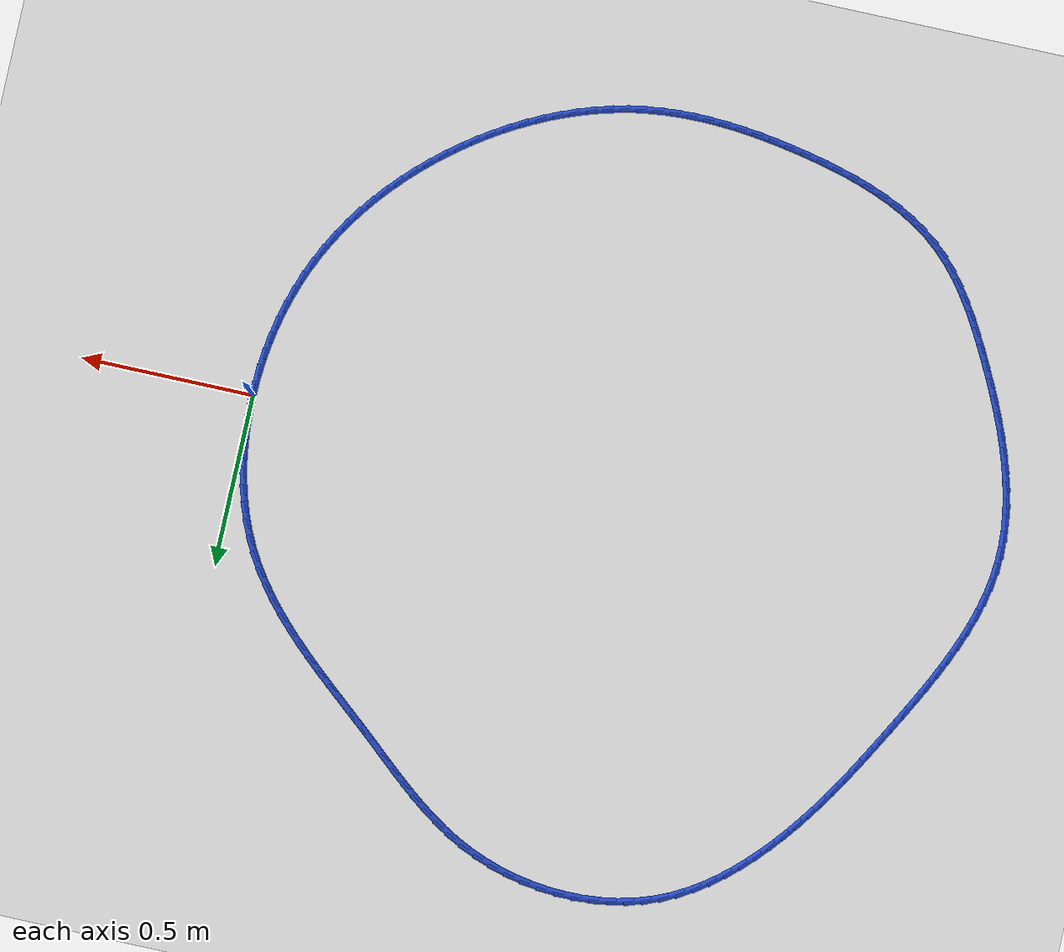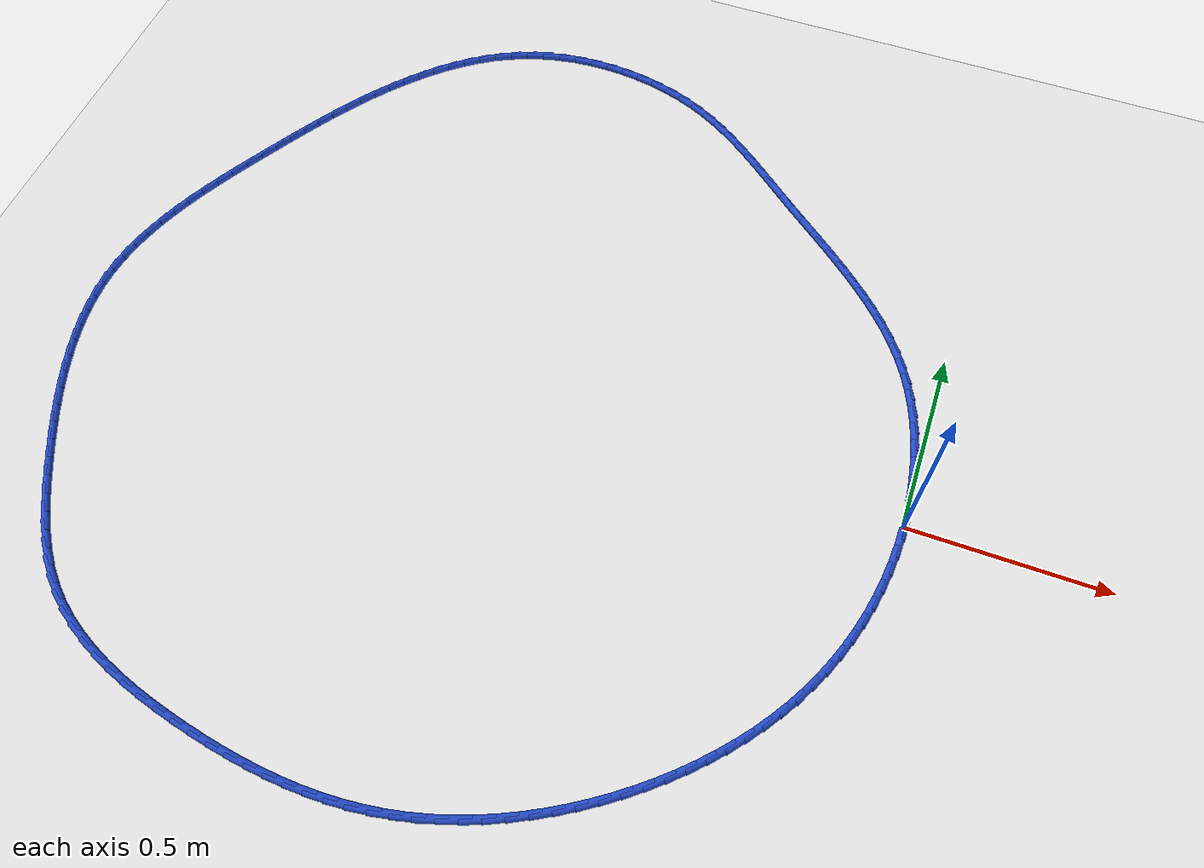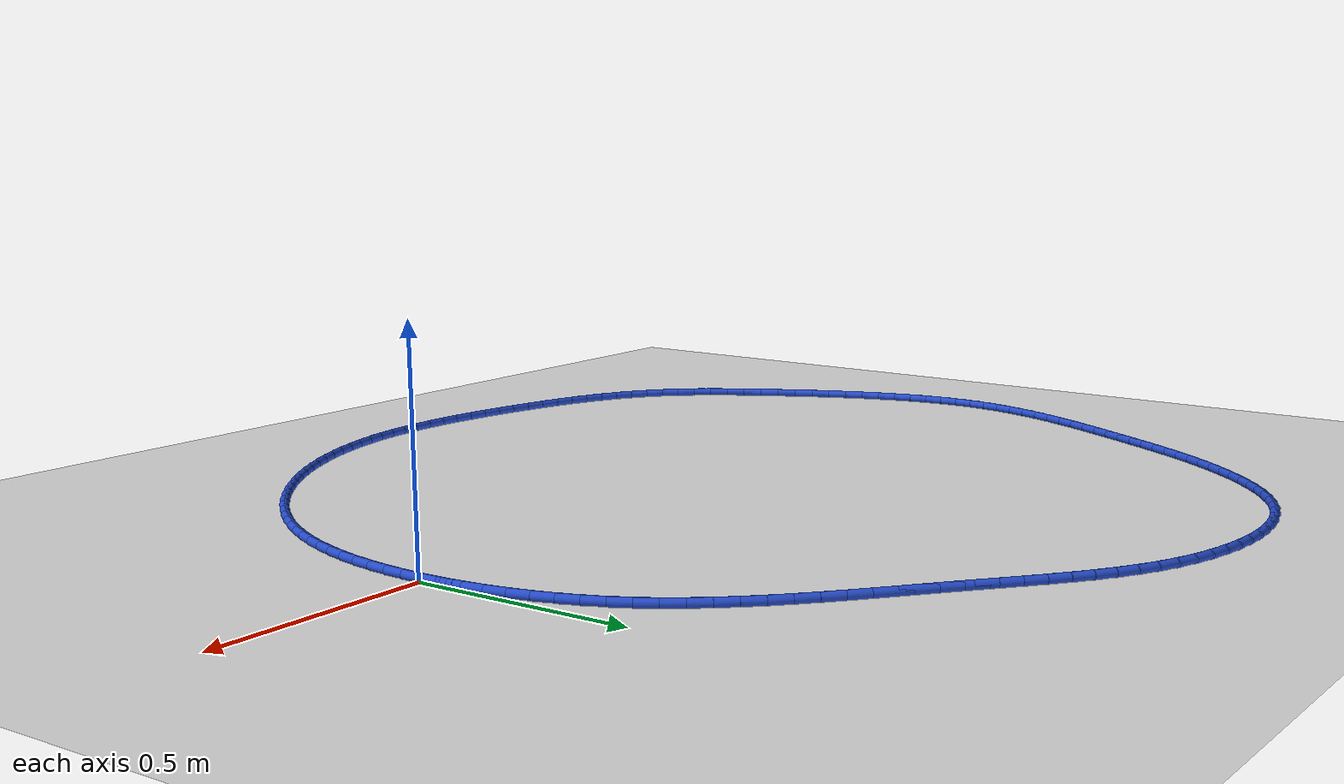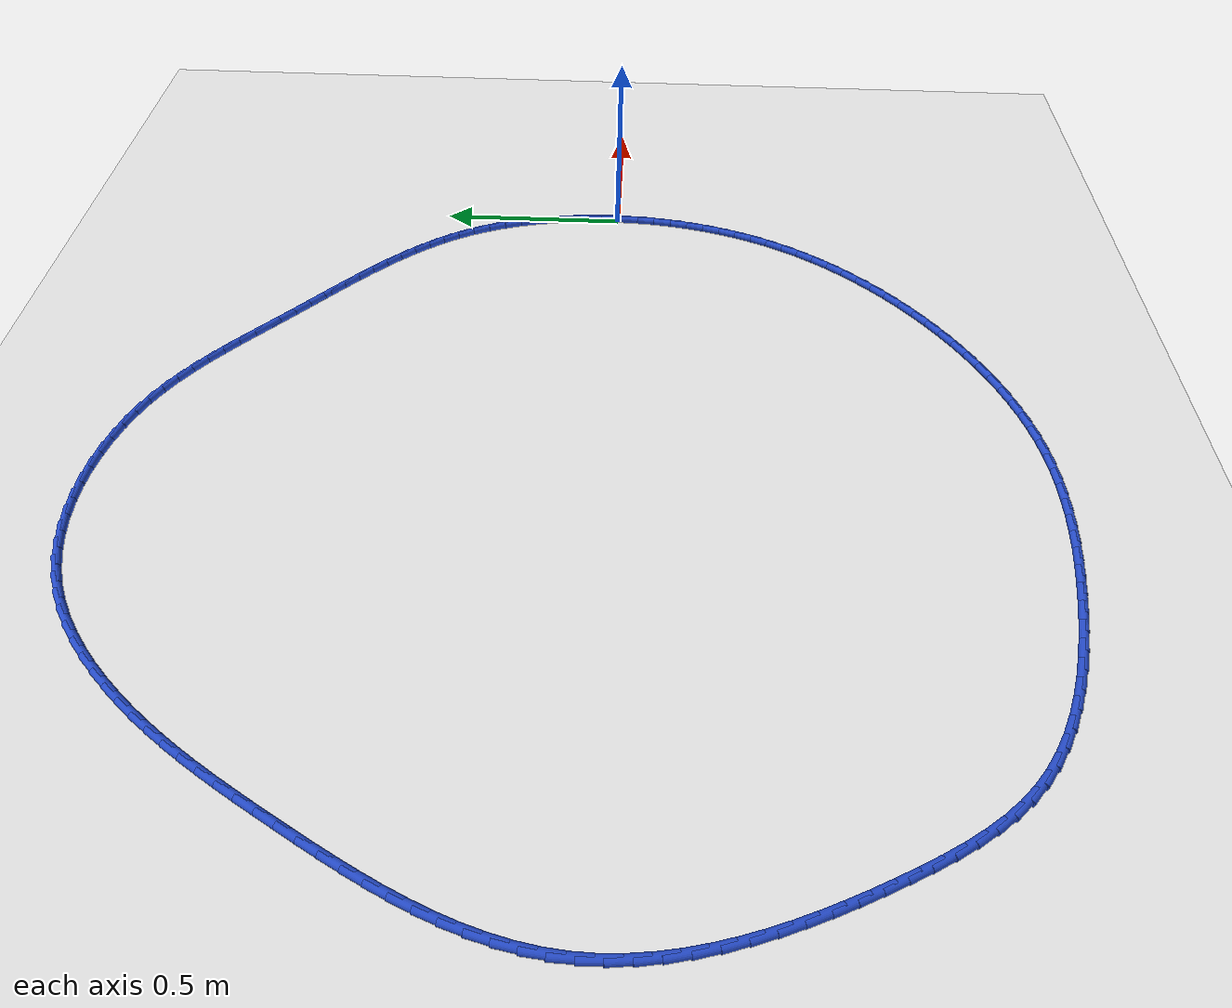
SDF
<sdf version="1.6">
 <world name="default">
  <light name="sun" type="directional">
   <pose>0 0 10 0 -0 0</pose>
   <diffuse>0.8 0.8 0.8 1</diffuse>
   <specular>0.2 0.2 0.2 1</specular>
   <attenuation>
    <range>1000</range>
    <constant>0.9</constant>
    <linear>0.01</linear>
    <quadratic>0.001</quadratic>
   </attenuation>
   <direction>-0.5 0.1 -0.9</direction>
  </light>
  <model name="ground_plane">
   <static>1</static>
   <link name="link">
    <collision name="collision">
     <geometry><plane><normal>0 0 1</normal><size>100 100</size></plane></geometry>
     <surface><friction><ode><mu>100</mu><mu2>50</mu2></ode></friction></surface>
    </collision>
    <visual name="visual">
     <cast_shadows>0</cast_shadows>
     <geometry><plane><normal>0 0 1</normal><size>100 100</size></plane></geometry>
     <material>
      <script><uri>file://media/materials/scripts/gazebo.material</uri><name>Gazebo/WhiteGlow</name></script>
     </material>
    </visual>
   </link>
  </model>
  <gravity>0 0 -9.8</gravity>
  <magnetic_field>6e-06 2.3e-05 -4.2e-05</magnetic_field>
  <atmosphere type="adiabatic"/>
  <physics name="default_physics" default="0" type="ode">
   <max_step_size>0.001</max_step_size>
   <real_time_factor>1</real_time_factor>
   <real_time_update_rate>1000</real_time_update_rate>
  </physics>
  <scene><ambient>0.4 0.4 0.4 1</ambient><background>0.7 0.7 0.7 1</background><shadows>1</shadows></scene>
  <spherical_coordinates>
   <surface_model>EARTH_WGS84</surface_model>
   <latitude_deg>0</latitude_deg>
   <longitude_deg>0</longitude_deg>
   <elevation>0</elevation>
   <heading_deg>0</heading_deg>
  </spherical_coordinates>
  <model name="line">
   <link name="link_0">
    <pose>-1.5612511283791264e-17 1.3877787807814457e-17 0.01 0 1.57 -1.5564989843207722</pose>
    <collision name="collision">
     <geometry><cylinder><radius>0.01</radius><length>0.08</length></cylinder></geometry>
    </collision>
    <visual name="visual">
     <material>
      <script><name>Gazebo/Blue</name><uri>file://media/materials/scripts/gazebo.material</uri></script>
     </material>
     <geometry><cylinder><radius>0.01</radius><length>0.08</length></cylinder></geometry>
    </visual>
   </link>
   <link name="link_1">
    <pose>-0.0007098977526530641 0.04964904367822557 0.01 0 1.57 -1.5098913511678889</pose>
    <collision name="collision">
     <geometry><cylinder><radius>0.01</radius><length>0.08</length></cylinder></geometry>
    </collision>
    <visual name="visual">
     <material>
      <script><name>Gazebo/Blue</name><uri>file://media/materials/scripts/gazebo.material</uri></script>
     </material>
     <geometry><cylinder><radius>0.01</radius><length>0.08</length></cylinder></geometry>
    </visual>
   </link>
   <link name="link_2">
    <pose>-0.0037348885526283983 0.09925499995855847 0.01 0 1.57 -1.461689081977313</pose>
    <collision name="collision">
     <geometry><cylinder><radius>0.01</radius><length>0.08</length></cylinder></geometry>
    </collision>
    <visual name="visual">
     <material>
      <script><name>Gazebo/Blue</name><uri>file://media/materials/scripts/gazebo.material</uri></script>
     </material>
     <geometry><cylinder><radius>0.01</radius><length>0.08</length></cylinder></geometry>
    </visual>
   </link>
   <link name="link_3">
    <pose>-0.00913995167566396 0.14859726037698096 0.01 0 1.57 -1.4114857236044163</pose>
    <collision name="collision">
     <geometry><cylinder><radius>0.01</radius><length>0.08</length></cylinder></geometry>
    </collision>
    <visual name="visual">
     <material>
      <script><name>Gazebo/Blue</name><uri>file://media/materials/scripts/gazebo.material</uri></script>
     </material>
     <geometry><cylinder><radius>0.01</radius><length>0.08</length></cylinder></geometry>
    </visual>
   </link>
   <link name="link_4">
    <pose>-0.01699006639749768 0.19745521646947506 0.01 0 1.57 -1.358876434776955</pose>
    <collision name="collision">
     <geometry><cylinder><radius>0.01</radius><length>0.08</length></cylinder></geometry>
    </collision>
    <visual name="visual">
     <material>
      <script><name>Gazebo/Blue</name><uri>file://media/materials/scripts/gazebo.material</uri></script>
     </material>
     <geometry><cylinder><radius>0.01</radius><length>0.08</length></cylinder></geometry>
    </visual>
   </link>
   <link name="link_5">
    <pose>-0.02735021199386751 0.245608259772023 0.01 0 1.57 -1.303462174925534</pose>
    <collision name="collision">
     <geometry><cylinder><radius>0.01</radius><length>0.08</length></cylinder></geometry>
    </collision>
    <visual name="visual">
     <material>
      <script><name>Gazebo/Blue</name><uri>file://media/materials/scripts/gazebo.material</uri></script>
     </material>
     <geometry><cylinder><radius>0.01</radius><length>0.08</length></cylinder></geometry>
    </visual>
   </link>
   <link name="link_6">
    <pose>-0.04028536774051138 0.292835781820607 0.01 0 1.57 -1.244858785908158</pose>
    <collision name="collision">
     <geometry><cylinder><radius>0.01</radius><length>0.08</length></cylinder></geometry>
    </collision>
    <visual name="visual">
     <material>
      <script><name>Gazebo/Blue</name><uri>file://media/materials/scripts/gazebo.material</uri></script>
     </material>
     <geometry><cylinder><radius>0.01</radius><length>0.08</length></cylinder></geometry>
    </visual>
   </link>
   <link name="link_7">
    <pose>-0.05586051291316721 0.3389171741512089 0.01 0 1.57 -1.1827122122715916</pose>
    <collision name="collision">
     <geometry><cylinder><radius>0.01</radius><length>0.08</length></cylinder></geometry>
    </collision>
    <visual name="visual">
     <material>
      <script><name>Gazebo/Blue</name><uri>file://media/materials/scripts/gazebo.material</uri></script>
     </material>
     <geometry><cylinder><radius>0.01</radius><length>0.08</length></cylinder></geometry>
    </visual>
   </link>
   <link name="link_8">
    <pose>-0.074140626787573 0.38363182829981124 0.01 0 1.57 -1.1167210165554227</pose>
    <collision name="collision">
     <geometry><cylinder><radius>0.01</radius><length>0.08</length></cylinder></geometry>
    </collision>
    <visual name="visual">
     <material>
      <script><name>Gazebo/Blue</name><uri>file://media/materials/scripts/gazebo.material</uri></script>
     </material>
     <geometry><cylinder><radius>0.01</radius><length>0.08</length></cylinder></geometry>
    </visual>
   </link>
   <link name="link_9">
    <pose>-0.09519068863946656 0.4267591358023958 0.01 0 1.57 -1.0476341555985051</pose>
    <collision name="collision">
     <geometry><cylinder><radius>0.01</radius><length>0.08</length></cylinder></geometry>
    </collision>
    <visual name="visual">
     <material>
      <script><name>Gazebo/Blue</name><uri>file://media/materials/scripts/gazebo.material</uri></script>
     </material>
     <geometry><cylinder><radius>0.01</radius><length>0.08</length></cylinder></geometry>
    </visual>
   </link>
   <link name="link_10">
    <pose>-0.11904393571678058 0.46811586092543533 0.01 0 1.57 -0.9820715219565893</pose>
    <collision name="collision">
     <geometry><cylinder><radius>0.01</radius><length>0.08</length></cylinder></geometry>
    </collision>
    <visual name="visual">
     <material>
      <script><name>Gazebo/Blue</name><uri>file://media/materials/scripts/gazebo.material</uri></script>
     </material>
     <geometry><cylinder><radius>0.01</radius><length>0.08</length></cylinder></geometry>
    </visual>
   </link>
   <link name="link_11">
    <pose>-0.14552089095877485 0.5077692155305663 0.01 0 1.57 -0.9232161957709449</pose>
    <collision name="collision">
     <geometry><cylinder><radius>0.01</radius><length>0.08</length></cylinder></geometry>
    </collision>
    <visual name="visual">
     <material>
      <script><name>Gazebo/Blue</name><uri>file://media/materials/scripts/gazebo.material</uri></script>
     </material>
     <geometry><cylinder><radius>0.01</radius><length>0.08</length></cylinder></geometry>
    </visual>
   </link>
   <link name="link_12">
    <pose>-0.17435467349826453 0.5458893198040637 0.01 0 1.57 -0.8713819181476368</pose>
    <collision name="collision">
     <geometry><cylinder><radius>0.01</radius><length>0.08</length></cylinder></geometry>
    </collision>
    <visual name="visual">
     <material>
      <script><name>Gazebo/Blue</name><uri>file://media/materials/scripts/gazebo.material</uri></script>
     </material>
     <geometry><cylinder><radius>0.01</radius><length>0.08</length></cylinder></geometry>
    </visual>
   </link>
   <link name="link_13">
    <pose>-0.20527813430308509 0.5826466096668362 0.01 0 1.57 -0.8266408173221186</pose>
    <collision name="collision">
     <geometry><cylinder><radius>0.01</radius><length>0.08</length></cylinder></geometry>
    </collision>
    <visual name="visual">
     <material>
      <script><name>Gazebo/Blue</name><uri>file://media/materials/scripts/gazebo.material</uri></script>
     </material>
     <geometry><cylinder><radius>0.01</radius><length>0.08</length></cylinder></geometry>
    </visual>
   </link>
   <link name="link_14">
    <pose>-0.23802412434107206 0.6182115210397927 0.01 0 1.57 -0.7889074943987042</pose>
    <collision name="collision">
     <geometry><cylinder><radius>0.01</radius><length>0.08</length></cylinder></geometry>
    </collision>
    <visual name="visual">
     <material>
      <script><name>Gazebo/Blue</name><uri>file://media/materials/scripts/gazebo.material</uri></script>
     </material>
     <geometry><cylinder><radius>0.01</radius><length>0.08</length></cylinder></geometry>
    </visual>
   </link>
   <link name="link_15">
    <pose>-0.27232549458006106 0.6527544898438419 0.01 0 1.57 -0.7580073522105671</pose>
    <collision name="collision">
     <geometry><cylinder><radius>0.01</radius><length>0.08</length></cylinder></geometry>
    </collision>
    <visual name="visual">
     <material>
      <script><name>Gazebo/Blue</name><uri>file://media/materials/scripts/gazebo.material</uri></script>
     </material>
     <geometry><cylinder><radius>0.01</radius><length>0.08</length></cylinder></geometry>
    </visual>
   </link>
   <link name="link_16">
    <pose>-0.3079150959878875 0.6864459519998917 0.01 0 1.57 -0.7337315099448477</pose>
    <collision name="collision">
     <geometry><cylinder><radius>0.01</radius><length>0.08</length></cylinder></geometry>
    </collision>
    <visual name="visual">
     <material>
      <script><name>Gazebo/Blue</name><uri>file://media/materials/scripts/gazebo.material</uri></script>
     </material>
     <geometry><cylinder><radius>0.01</radius><length>0.08</length></cylinder></geometry>
    </visual>
   </link>
   <link name="link_17">
    <pose>-0.34452577953238706 0.7194563434288512 0.01 0 1.57 -0.7158774652776898</pose>
    <collision name="collision">
     <geometry><cylinder><radius>0.01</radius><length>0.08</length></cylinder></geometry>
    </collision>
    <visual name="visual">
     <material>
      <script><name>Gazebo/Blue</name><uri>file://media/materials/scripts/gazebo.material</uri></script>
     </material>
     <geometry><cylinder><radius>0.01</radius><length>0.08</length></cylinder></geometry>
    </visual>
   </link>
   <link name="link_18">
    <pose>-0.3818903961813949 0.7519561000516289 0.01 0 1.57 -0.7042772592036856</pose>
    <collision name="collision">
     <geometry><cylinder><radius>0.01</radius><length>0.08</length></cylinder></geometry>
    </collision>
    <visual name="visual">
     <material>
      <script><name>Gazebo/Blue</name><uri>file://media/materials/scripts/gazebo.material</uri></script>
     </material>
     <geometry><cylinder><radius>0.01</radius><length>0.08</length></cylinder></geometry>
    </visual>
   </link>
   <link name="link_19">
    <pose>-0.41974179690274716 0.7841156577891337 0.01 0 1.57 -0.6988157278524184</pose>
    <collision name="collision">
     <geometry><cylinder><radius>0.01</radius><length>0.08</length></cylinder></geometry>
    </collision>
    <visual name="visual">
     <material>
      <script><name>Gazebo/Blue</name><uri>file://media/materials/scripts/gazebo.material</uri></script>
     </material>
     <geometry><cylinder><radius>0.01</radius><length>0.08</length></cylinder></geometry>
    </visual>
   </link>
   <link name="link_20">
    <pose>-0.45781283266427897 0.816105452562274 0.01 0 1.57 -0.6994412259201085</pose>
    <collision name="collision">
     <geometry><cylinder><radius>0.01</radius><length>0.08</length></cylinder></geometry>
    </collision>
    <visual name="visual">
     <material>
      <script><name>Gazebo/Blue</name><uri>file://media/materials/scripts/gazebo.material</uri></script>
     </material>
     <geometry><cylinder><radius>0.01</radius><length>0.08</length></cylinder></geometry>
    </visual>
   </link>
   <link name="link_21">
    <pose>-0.4958363544338257 0.848095920291958 0.01 0 1.57 -0.7061385388451107</pose>
    <collision name="collision">
     <geometry><cylinder><radius>0.01</radius><length>0.08</length></cylinder></geometry>
    </collision>
    <visual name="visual">
     <material>
      <script><name>Gazebo/Blue</name><uri>file://media/materials/scripts/gazebo.material</uri></script>
     </material>
     <geometry><cylinder><radius>0.01</radius><length>0.08</length></cylinder></geometry>
    </visual>
   </link>
   <link name="link_22">
    <pose>-0.5335463627830518 0.880256394657043 0.01 0 1.57 -0.7142990602482188</pose>
    <collision name="collision">
     <geometry><cylinder><radius>0.01</radius><length>0.08</length></cylinder></geometry>
    </collision>
    <visual name="visual">
     <material>
      <script><name>Gazebo/Blue</name><uri>file://media/materials/scripts/gazebo.material</uri></script>
     </material>
     <geometry><cylinder><radius>0.01</radius><length>0.08</length></cylinder></geometry>
    </visual>
   </link>
   <link name="link_23">
    <pose>-0.5708447278686133 0.9125952557006942 0.01 0 1.57 -0.7143437357718527</pose>
    <collision name="collision">
     <geometry><cylinder><radius>0.01</radius><length>0.08</length></cylinder></geometry>
    </collision>
    <visual name="visual">
     <material>
      <script><name>Gazebo/Blue</name><uri>file://media/materials/scripts/gazebo.material</uri></script>
     </material>
     <geometry><cylinder><radius>0.01</radius><length>0.08</length></cylinder></geometry>
    </visual>
   </link>
   <link name="link_24">
    <pose>-0.6079760949042965 0.9447922301744632 0.01 0 1.57 -0.7049847693766452</pose>
    <collision name="collision">
     <geometry><cylinder><radius>0.01</radius><length>0.08</length></cylinder></geometry>
    </collision>
    <visual name="visual">
     <material>
      <script><name>Gazebo/Blue</name><uri>file://media/materials/scripts/gazebo.material</uri></script>
     </material>
     <geometry><cylinder><radius>0.01</radius><length>0.08</length></cylinder></geometry>
    </visual>
   </link>
   <link name="link_25">
    <pose>-0.6452269343424237 0.9764869427220277 0.01 0 1.57 -0.6860790593038789</pose>
    <collision name="collision">
     <geometry><cylinder><radius>0.01</radius><length>0.08</length></cylinder></geometry>
    </collision>
    <visual name="visual">
     <material>
      <script><name>Gazebo/Blue</name><uri>file://media/materials/scripts/gazebo.material</uri></script>
     </material>
     <geometry><cylinder><radius>0.01</radius><length>0.08</length></cylinder></geometry>
    </visual>
   </link>
   <link name="link_26">
    <pose>-0.682883716635318 1.0073190179870664 0.01 0 1.57 -0.6574899913007259</pose>
    <collision name="collision">
     <geometry><cylinder><radius>0.01</radius><length>0.08</length></cylinder></geometry>
    </collision>
    <visual name="visual">
     <material>
      <script><name>Gazebo/Blue</name><uri>file://media/materials/scripts/gazebo.material</uri></script>
     </material>
     <geometry><cylinder><radius>0.01</radius><length>0.08</length></cylinder></geometry>
    </visual>
   </link>
   <link name="link_27">
    <pose>-0.7212329122353013 1.0369280806132568 0.01 0 1.57 -0.6191405631445258</pose>
    <collision name="collision">
     <geometry><cylinder><radius>0.01</radius><length>0.08</length></cylinder></geometry>
    </collision>
    <visual name="visual">
     <material>
      <script><name>Gazebo/Blue</name><uri>file://media/materials/scripts/gazebo.material</uri></script>
     </material>
     <geometry><cylinder><radius>0.01</radius><length>0.08</length></cylinder></geometry>
    </visual>
   </link>
   <link name="link_28">
    <pose>-0.7605609915946963 1.0649537552442772 0.01 0 1.57 -0.5710957198359372</pose>
    <collision name="collision">
     <geometry><cylinder><radius>0.01</radius><length>0.08</length></cylinder></geometry>
    </collision>
    <visual name="visual">
     <material>
      <script><name>Gazebo/Blue</name><uri>file://media/materials/scripts/gazebo.material</uri></script>
     </material>
     <geometry><cylinder><radius>0.01</radius><length>0.08</length></cylinder></geometry>
    </visual>
   </link>
   <link name="link_29">
    <pose>-0.8011544251658256 1.0910356665238055 0.01 0 1.57 -0.5136694395763259</pose>
    <collision name="collision">
     <geometry><cylinder><radius>0.01</radius><length>0.08</length></cylinder></geometry>
    </collision>
    <visual name="visual">
     <material>
      <script><name>Gazebo/Blue</name><uri>file://media/materials/scripts/gazebo.material</uri></script>
     </material>
     <geometry><cylinder><radius>0.01</radius><length>0.08</length></cylinder></geometry>
    </visual>
   </link>
   <link name="link_30">
    <pose>-0.8432996834010119 1.1148134390955202 0.01 0 1.57 -0.4475956365622116</pose>
    <collision name="collision">
     <geometry><cylinder><radius>0.01</radius><length>0.08</length></cylinder></geometry>
    </collision>
    <visual name="visual">
     <material>
      <script><name>Gazebo/Blue</name><uri>file://media/materials/scripts/gazebo.material</uri></script>
     </material>
     <geometry><cylinder><radius>0.01</radius><length>0.08</length></cylinder></geometry>
    </visual>
   </link>
   <link name="link_31">
    <pose>-0.8872800356547518 1.1359281026238215 0.01 0 1.57 -0.3775048325289558</pose>
    <collision name="collision">
     <geometry><cylinder><radius>0.01</radius><length>0.08</length></cylinder></geometry>
    </collision>
    <visual name="visual">
     <material>
      <script><name>Gazebo/Blue</name><uri>file://media/materials/scripts/gazebo.material</uri></script>
     </material>
     <geometry><cylinder><radius>0.01</radius><length>0.08</length></cylinder></geometry>
    </visual>
   </link>
   <link name="link_32">
    <pose>-0.933155410529325 1.1541187151377945 0.01 0 1.57 -0.3092686187401753</pose>
    <collision name="collision">
     <geometry><cylinder><radius>0.01</radius><length>0.08</length></cylinder></geometry>
    </collision>
    <visual name="visual">
     <material>
      <script><name>Gazebo/Blue</name><uri>file://media/materials/scripts/gazebo.material</uri></script>
     </material>
     <geometry><cylinder><radius>0.01</radius><length>0.08</length></cylinder></geometry>
    </visual>
   </link>
   <link name="link_33">
    <pose>-0.9806202668066696 1.1692847460937932 0.01 0 1.57 -0.24260107318995597</pose>
    <collision name="collision">
     <geometry><cylinder><radius>0.01</radius><length>0.08</length></cylinder></geometry>
    </collision>
    <visual name="visual">
     <material>
      <script><name>Gazebo/Blue</name><uri>file://media/materials/scripts/gazebo.material</uri></script>
     </material>
     <geometry><cylinder><radius>0.01</radius><length>0.08</length></cylinder></geometry>
    </visual>
   </link>
   <link name="link_34">
    <pose>-1.0293352568735465 1.181340503196908 0.01 0 1.57 -0.17667068221247198</pose>
    <collision name="collision">
     <geometry><cylinder><radius>0.01</radius><length>0.08</length></cylinder></geometry>
    </collision>
    <visual name="visual">
     <material>
      <script><name>Gazebo/Blue</name><uri>file://media/materials/scripts/gazebo.material</uri></script>
     </material>
     <geometry><cylinder><radius>0.01</radius><length>0.08</length></cylinder></geometry>
    </visual>
   </link>
   <link name="link_35">
    <pose>-1.0789610331167172 1.1902002941522312 0.01 0 1.57 -0.11067029161736543</pose>
    <collision name="collision">
     <geometry><cylinder><radius>0.01</radius><length>0.08</length></cylinder></geometry>
    </collision>
    <visual name="visual">
     <material>
      <script><name>Gazebo/Blue</name><uri>file://media/materials/scripts/gazebo.material</uri></script>
     </material>
     <geometry><cylinder><radius>0.01</radius><length>0.08</length></cylinder></geometry>
    </visual>
   </link>
   <link name="link_36">
    <pose>-1.1291582479229436 1.1957784266648555 0.01 0 1.57 -0.04381117464663719</pose>
    <collision name="collision">
     <geometry><cylinder><radius>0.01</radius><length>0.08</length></cylinder></geometry>
    </collision>
    <visual name="visual">
     <material>
      <script><name>Gazebo/Blue</name><uri>file://media/materials/scripts/gazebo.material</uri></script>
     </material>
     <geometry><cylinder><radius>0.01</radius><length>0.08</length></cylinder></geometry>
    </visual>
   </link>
   <link name="link_37">
    <pose>-1.1795875536789868 1.1979892084398718 0.01 0 1.57 0.024681208804191484</pose>
    <collision name="collision">
     <geometry><cylinder><radius>0.01</radius><length>0.08</length></cylinder></geometry>
    </collision>
    <visual name="visual">
     <material>
      <script><name>Gazebo/Blue</name><uri>file://media/materials/scripts/gazebo.material</uri></script>
     </material>
     <geometry><cylinder><radius>0.01</radius><length>0.08</length></cylinder></geometry>
    </visual>
   </link>
   <link name="link_38">
    <pose>-1.2299096027716079 1.196746947182372 0.01 0 1.57 0.09556672202371244</pose>
    <collision name="collision">
     <geometry><cylinder><radius>0.01</radius><length>0.08</length></cylinder></geometry>
    </collision>
    <visual name="visual">
     <material>
      <script><name>Gazebo/Blue</name><uri>file://media/materials/scripts/gazebo.material</uri></script>
     </material>
     <geometry><cylinder><radius>0.01</radius><length>0.08</length></cylinder></geometry>
    </visual>
   </link>
   <link name="link_39">
    <pose>-1.2797850475875692 1.1919659505974478 0.01 0 1.57 0.169582007312785</pose>
    <collision name="collision">
     <geometry><cylinder><radius>0.01</radius><length>0.08</length></cylinder></geometry>
    </collision>
    <visual name="visual">
     <material>
      <script><name>Gazebo/Blue</name><uri>file://media/materials/scripts/gazebo.material</uri></script>
     </material>
     <geometry><cylinder><radius>0.01</radius><length>0.08</length></cylinder></geometry>
    </visual>
   </link>
   <link name="link_40">
    <pose>-1.3288745405136315 1.183560526390192 0.01 0 1.57 0.2474200830752982</pose>
    <collision name="collision">
     <geometry><cylinder><radius>0.01</radius><length>0.08</length></cylinder></geometry>
    </collision>
    <visual name="visual">
     <material>
      <script><name>Gazebo/Blue</name><uri>file://media/materials/scripts/gazebo.material</uri></script>
     </material>
     <geometry><cylinder><radius>0.01</radius><length>0.08</length></cylinder></geometry>
    </visual>
   </link>
   <link name="link_41">
    <pose>-1.3768387339365566 1.1714449822656958 0.01 0 1.57 0.32969403792582797</pose>
    <collision name="collision">
     <geometry><cylinder><radius>0.01</radius><length>0.08</length></cylinder></geometry>
    </collision>
    <visual name="visual">
     <material>
      <script><name>Gazebo/Blue</name><uri>file://media/materials/scripts/gazebo.material</uri></script>
     </material>
     <geometry><cylinder><radius>0.01</radius><length>0.08</length></cylinder></geometry>
    </visual>
   </link>
   <link name="link_42">
    <pose>-1.4233382802431054 1.155533625929051 0.01 0 1.57 0.41639448822839126</pose>
    <collision name="collision">
     <geometry><cylinder><radius>0.01</radius><length>0.08</length></cylinder></geometry>
    </collision>
    <visual name="visual">
     <material>
      <script><name>Gazebo/Blue</name><uri>file://media/materials/scripts/gazebo.material</uri></script>
     </material>
     <geometry><cylinder><radius>0.01</radius><length>0.08</length></cylinder></geometry>
    </visual>
   </link>
   <link name="link_43">
    <pose>-1.468048263827069 1.1357604152171277 0.01 0 1.57 0.5007324691013504</pose>
    <collision name="collision">
     <geometry><cylinder><radius>0.01</radius><length>0.08</length></cylinder></geometry>
    </collision>
    <visual name="visual">
     <material>
      <script><name>Gazebo/Blue</name><uri>file://media/materials/scripts/gazebo.material</uri></script>
     </material>
     <geometry><cylinder><radius>0.01</radius><length>0.08</length></cylinder></geometry>
    </visual>
   </link>
   <link name="link_44">
    <pose>-1.510848371427963 1.1123378875882837 0.01 0 1.57 0.5772904926550719</pose>
    <collision name="collision">
     <geometry><cylinder><radius>0.01</radius><length>0.08</length></cylinder></geometry>
    </collision>
    <visual name="visual">
     <material>
      <script><name>Gazebo/Blue</name><uri>file://media/materials/scripts/gazebo.material</uri></script>
     </material>
     <geometry><cylinder><radius>0.01</radius><length>0.08</length></cylinder></geometry>
    </visual>
   </link>
   <link name="link_45">
    <pose>-1.5517701859929471 1.0856853972305751 0.01 0 1.57 0.6459397193873888</pose>
    <collision name="collision">
     <geometry><cylinder><radius>0.01</radius><length>0.08</length></cylinder></geometry>
    </collision>
    <visual name="visual">
     <material>
      <script><name>Gazebo/Blue</name><uri>file://media/materials/scripts/gazebo.material</uri></script>
     </material>
     <geometry><cylinder><radius>0.01</radius><length>0.08</length></cylinder></geometry>
    </visual>
   </link>
   <link name="link_46">
    <pose>-1.5908488871828812 1.0562271954955658 0.01 0 1.57 0.7069734357951066</pose>
    <collision name="collision">
     <geometry><cylinder><radius>0.01</radius><length>0.08</length></cylinder></geometry>
    </collision>
    <visual name="visual">
     <material>
      <script><name>Gazebo/Blue</name><uri>file://media/materials/scripts/gazebo.material</uri></script>
     </material>
     <geometry><cylinder><radius>0.01</radius><length>0.08</length></cylinder></geometry>
    </visual>
   </link>
   <link name="link_47">
    <pose>-1.6281196546586256 1.0243875337348196 0.01 0 1.57 0.7608537630905128</pose>
    <collision name="collision">
     <geometry><cylinder><radius>0.01</radius><length>0.08</length></cylinder></geometry>
    </collision>
    <visual name="visual">
     <material>
      <script><name>Gazebo/Blue</name><uri>file://media/materials/scripts/gazebo.material</uri></script>
     </material>
     <geometry><cylinder><radius>0.01</radius><length>0.08</length></cylinder></geometry>
    </visual>
   </link>
   <link name="link_48">
    <pose>-1.663617668081039 0.9905906632998982 0.01 0 1.57 0.8081093058366904</pose>
    <collision name="collision">
     <geometry><cylinder><radius>0.01</radius><length>0.08</length></cylinder></geometry>
    </collision>
    <visual name="visual">
     <material>
      <script><name>Gazebo/Blue</name><uri>file://media/materials/scripts/gazebo.material</uri></script>
     </material>
     <geometry><cylinder><radius>0.01</radius><length>0.08</length></cylinder></geometry>
    </visual>
   </link>
   <link name="link_49">
    <pose>-1.6973781071109797 0.9552608355423652 0.01 0 1.57 0.8495767584016871</pose>
    <collision name="collision">
     <geometry><cylinder><radius>0.01</radius><length>0.08</length></cylinder></geometry>
    </collision>
    <visual name="visual">
     <material>
      <script><name>Gazebo/Blue</name><uri>file://media/materials/scripts/gazebo.material</uri></script>
     </material>
     <geometry><cylinder><radius>0.01</radius><length>0.08</length></cylinder></geometry>
    </visual>
   </link>
   <link name="link_50">
    <pose>-1.7294510966208987 0.9187822520052912 0.01 0 1.57 0.8873133953211949</pose>
    <collision name="collision">
     <geometry><cylinder><radius>0.01</radius><length>0.08</length></cylinder></geometry>
    </collision>
    <visual name="visual">
     <material>
      <script><name>Gazebo/Blue</name><uri>file://media/materials/scripts/gazebo.material</uri></script>
     </material>
     <geometry><cylinder><radius>0.01</radius><length>0.08</length></cylinder></geometry>
    </visual>
   </link>
   <link name="link_51">
    <pose>-1.7599742283656894 0.8813047226428199 0.01 0 1.57 0.9217562369393135</pose>
    <collision name="collision">
     <geometry><cylinder><radius>0.01</radius><length>0.08</length></cylinder></geometry>
    </collision>
    <visual name="visual">
     <material>
      <script><name>Gazebo/Blue</name><uri>file://media/materials/scripts/gazebo.material</uri></script>
     </material>
     <geometry><cylinder><radius>0.01</radius><length>0.08</length></cylinder></geometry>
    </visual>
   </link>
   <link name="link_52">
    <pose>-1.7891168188324325 0.8428930422561897 0.01 0 1.57 0.9526834847132468</pose>
    <collision name="collision">
     <geometry><cylinder><radius>0.01</radius><length>0.08</length></cylinder></geometry>
    </collision>
    <visual name="visual">
     <material>
      <script><name>Gazebo/Blue</name><uri>file://media/materials/scripts/gazebo.material</uri></script>
     </material>
     <geometry><cylinder><radius>0.01</radius><length>0.08</length></cylinder></geometry>
    </visual>
   </link>
   <link name="link_53">
    <pose>-1.8170482289391308 0.8036118865817466 0.01 0 1.57 0.9799388127509421</pose>
    <collision name="collision">
     <geometry><cylinder><radius>0.01</radius><length>0.08</length></cylinder></geometry>
    </collision>
    <visual name="visual">
     <material>
      <script><name>Gazebo/Blue</name><uri>file://media/materials/scripts/gazebo.material</uri></script>
     </material>
     <geometry><cylinder><radius>0.01</radius><length>0.08</length></cylinder></geometry>
    </visual>
   </link>
   <link name="link_54">
    <pose>-1.8439378196037892 0.7635259313558358 0.01 0 1.57 1.0034240550342428</pose>
    <collision name="collision">
     <geometry><cylinder><radius>0.01</radius><length>0.08</length></cylinder></geometry>
    </collision>
    <visual name="visual">
     <material>
      <script><name>Gazebo/Blue</name><uri>file://media/materials/scripts/gazebo.material</uri></script>
     </material>
     <geometry><cylinder><radius>0.01</radius><length>0.08</length></cylinder></geometry>
    </visual>
   </link>
   <link name="link_55">
    <pose>-1.8699549517444132 0.722699852314802 0.01 0 1.57 1.0230896271923058</pose>
    <collision name="collision">
     <geometry><cylinder><radius>0.01</radius><length>0.08</length></cylinder></geometry>
    </collision>
    <visual name="visual">
     <material>
      <script><name>Gazebo/Blue</name><uri>file://media/materials/scripts/gazebo.material</uri></script>
     </material>
     <geometry><cylinder><radius>0.01</radius><length>0.08</length></cylinder></geometry>
    </visual>
   </link>
   <link name="link_56">
    <pose>-1.8952689862790049 0.6811983251949913 0.01 0 1.57 1.0389248412638683</pose>
    <collision name="collision">
     <geometry><cylinder><radius>0.01</radius><length>0.08</length></cylinder></geometry>
    </collision>
    <visual name="visual">
     <material>
      <script><name>Gazebo/Blue</name><uri>file://media/materials/scripts/gazebo.material</uri></script>
     </material>
     <geometry><cylinder><radius>0.01</radius><length>0.08</length></cylinder></geometry>
    </visual>
   </link>
   <link name="link_57">
    <pose>-1.9200492841255716 0.6390860257327488 0.01 0 1.57 1.050949002536453</pose>
    <collision name="collision">
     <geometry><cylinder><radius>0.01</radius><length>0.08</length></cylinder></geometry>
    </collision>
    <visual name="visual">
     <material>
      <script><name>Gazebo/Blue</name><uri>file://media/materials/scripts/gazebo.material</uri></script>
     </material>
     <geometry><cylinder><radius>0.01</radius><length>0.08</length></cylinder></geometry>
    </visual>
   </link>
   <link name="link_58">
    <pose>-1.9444652062021157 0.5964276296644199 0.01 0 1.57 1.0592038457666697</pose>
    <collision name="collision">
     <geometry><cylinder><radius>0.01</radius><length>0.08</length></cylinder></geometry>
    </collision>
    <visual name="visual">
     <material>
      <script><name>Gazebo/Blue</name><uri>file://media/materials/scripts/gazebo.material</uri></script>
     </material>
     <geometry><cylinder><radius>0.01</radius><length>0.08</length></cylinder></geometry>
    </visual>
   </link>
   <link name="link_59">
    <pose>-1.9686861134266413 0.5532878127263494 0.01 0 1.57 1.0641530904964682</pose>
    <collision name="collision">
     <geometry><cylinder><radius>0.01</radius><length>0.08</length></cylinder></geometry>
    </collision>
    <visual name="visual">
     <material>
      <script><name>Gazebo/Blue</name><uri>file://media/materials/scripts/gazebo.material</uri></script>
     </material>
     <geometry><cylinder><radius>0.01</radius><length>0.08</length></cylinder></geometry>
    </visual>
   </link>
   <link name="link_60">
    <pose>-1.992859440519224 0.5097291230249851 0.01 0 1.57 1.0709971600398125</pose>
    <collision name="collision">
     <geometry><cylinder><radius>0.01</radius><length>0.08</length></cylinder></geometry>
    </collision>
    <visual name="visual">
     <material>
      <script><name>Gazebo/Blue</name><uri>file://media/materials/scripts/gazebo.material</uri></script>
     </material>
     <geometry><cylinder><radius>0.01</radius><length>0.08</length></cylinder></geometry>
    </visual>
   </link>
   <link name="link_61">
    <pose>-2.01685365306206 0.4657870386256999 0.01 0 1.57 1.0832991205285547</pose>
    <collision name="collision">
     <geometry><cylinder><radius>0.01</radius><length>0.08</length></cylinder></geometry>
    </collision>
    <visual name="visual">
     <material>
      <script><name>Gazebo/Blue</name><uri>file://media/materials/scripts/gazebo.material</uri></script>
     </material>
     <geometry><cylinder><radius>0.01</radius><length>0.08</length></cylinder></geometry>
    </visual>
   </link>
   <link name="link_62">
    <pose>-2.0403451022061776 0.4214783955835661 0.01 0 1.57 1.101221303776828</pose>
    <collision name="collision">
     <geometry><cylinder><radius>0.01</radius><length>0.08</length></cylinder></geometry>
    </collision>
    <visual name="visual">
     <material>
      <script><name>Gazebo/Blue</name><uri>file://media/materials/scripts/gazebo.material</uri></script>
     </material>
     <geometry><cylinder><radius>0.01</radius><length>0.08</length></cylinder></geometry>
    </visual>
   </link>
   <link name="link_63">
    <pose>-2.0630063450753937 0.37681966179654125 0.01 0 1.57 1.1249529116845707</pose>
    <collision name="collision">
     <geometry><cylinder><radius>0.01</radius><length>0.08</length></cylinder></geometry>
    </collision>
    <visual name="visual">
     <material>
      <script><name>Gazebo/Blue</name><uri>file://media/materials/scripts/gazebo.material</uri></script>
     </material>
     <geometry><cylinder><radius>0.01</radius><length>0.08</length></cylinder></geometry>
    </visual>
   </link>
   <link name="link_64">
    <pose>-2.0845099387935324 0.3318273051625852 0.01 0 1.57 1.1547683860261622</pose>
    <collision name="collision">
     <geometry><cylinder><radius>0.01</radius><length>0.08</length></cylinder></geometry>
    </collision>
    <visual name="visual">
     <material>
      <script><name>Gazebo/Blue</name><uri>file://media/materials/scripts/gazebo.material</uri></script>
     </material>
     <geometry><cylinder><radius>0.01</radius><length>0.08</length></cylinder></geometry>
    </visual>
   </link>
   <link name="link_65">
    <pose>-2.104528440484414 0.2865177935796563 0.01 0 1.57 1.1910105168335872</pose>
    <collision name="collision">
     <geometry><cylinder><radius>0.01</radius><length>0.08</length></cylinder></geometry>
    </collision>
    <visual name="visual">
     <material>
      <script><name>Gazebo/Blue</name><uri>file://media/materials/scripts/gazebo.material</uri></script>
     </material>
     <geometry><cylinder><radius>0.01</radius><length>0.08</length></cylinder></geometry>
    </visual>
   </link>
   <link name="link_66">
    <pose>-2.1227344072718584 0.24090759494571273 0.01 0 1.57 1.234064385428644</pose>
    <collision name="collision">
     <geometry><cylinder><radius>0.01</radius><length>0.08</length></cylinder></geometry>
    </collision>
    <visual name="visual">
     <material>
      <script><name>Gazebo/Blue</name><uri>file://media/materials/scripts/gazebo.material</uri></script>
     </material>
     <geometry><cylinder><radius>0.01</radius><length>0.08</length></cylinder></geometry>
    </visual>
   </link>
   <link name="link_67">
    <pose>-2.1388003962796875 0.1950131771587141 0.01 0 1.57 1.2843170728541082</pose>
    <collision name="collision">
     <geometry><cylinder><radius>0.01</radius><length>0.08</length></cylinder></geometry>
    </collision>
    <visual name="visual">
     <material>
      <script><name>Gazebo/Blue</name><uri>file://media/materials/scripts/gazebo.material</uri></script>
     </material>
     <geometry><cylinder><radius>0.01</radius><length>0.08</length></cylinder></geometry>
    </visual>
   </link>
   <link name="link_68">
    <pose>-2.1523989646317214 0.1488510081166185 0.01 0 1.57 1.342097776611007</pose>
    <collision name="collision">
     <geometry><cylinder><radius>0.01</radius><length>0.08</length></cylinder></geometry>
    </collision>
    <visual name="visual">
     <material>
      <script><name>Gazebo/Blue</name><uri>file://media/materials/scripts/gazebo.material</uri></script>
     </material>
     <geometry><cylinder><radius>0.01</radius><length>0.08</length></cylinder></geometry>
    </visual>
   </link>
   <link name="link_69">
    <pose>-2.163202669451783 0.10243755571738533 0.01 0 1.57 1.4075945656852336</pose>
    <collision name="collision">
     <geometry><cylinder><radius>0.01</radius><length>0.08</length></cylinder></geometry>
    </collision>
    <visual name="visual">
     <material>
      <script><name>Gazebo/Blue</name><uri>file://media/materials/scripts/gazebo.material</uri></script>
     </material>
     <geometry><cylinder><radius>0.01</radius><length>0.08</length></cylinder></geometry>
    </visual>
   </link>
   <link name="link_70">
    <pose>-2.1708840678636907 0.05578928785897257 0.01 0 1.57 1.4807446278080458</pose>
    <collision name="collision">
     <geometry><cylinder><radius>0.01</radius><length>0.08</length></cylinder></geometry>
    </collision>
    <visual name="visual">
     <material>
      <script><name>Gazebo/Blue</name><uri>file://media/materials/scripts/gazebo.material</uri></script>
     </material>
     <geometry><cylinder><radius>0.01</radius><length>0.08</length></cylinder></geometry>
    </visual>
   </link>
   <link name="link_71">
    <pose>-2.1751159300494733 0.008922689165223733 0.01 0 1.57 1.5581462477677612</pose>
    <collision name="collision">
     <geometry><cylinder><radius>0.01</radius><length>0.08</length></cylinder></geometry>
    </collision>
    <visual name="visual">
     <material>
      <script><name>Gazebo/Blue</name><uri>file://media/materials/scripts/gazebo.material</uri></script>
     </material>
     <geometry><cylinder><radius>0.01</radius><length>0.08</length></cylinder></geometry>
    </visual>
   </link>
   <link name="link_72">
    <pose>-2.175711242106823 -0.03813474825442996 0.01 0 1.57 -1.5105609952214545</pose>
    <collision name="collision">
     <geometry><cylinder><radius>0.01</radius><length>0.08</length></cylinder></geometry>
    </collision>
    <visual name="visual">
     <material>
      <script><name>Gazebo/Blue</name><uri>file://media/materials/scripts/gazebo.material</uri></script>
     </material>
     <geometry><cylinder><radius>0.01</radius><length>0.08</length></cylinder></geometry>
    </visual>
   </link>
   <link name="link_73">
    <pose>-2.1728652472345336 -0.08532552364630551 0.01 0 1.57 -1.4439456758171754</pose>
    <collision name="collision">
     <geometry><cylinder><radius>0.01</radius><length>0.08</length></cylinder></geometry>
    </collision>
    <visual name="visual">
     <material>
      <script><name>Gazebo/Blue</name><uri>file://media/materials/scripts/gazebo.material</uri></script>
     </material>
     <geometry><cylinder><radius>0.01</radius><length>0.08</length></cylinder></geometry>
    </visual>
   </link>
   <link name="link_74">
    <pose>-2.1668377247913315 -0.1325870699213663 0.01 0 1.57 -1.3836874695277264</pose>
    <collision name="collision">
     <geometry><cylinder><radius>0.01</radius><length>0.08</length></cylinder></geometry>
    </collision>
    <visual name="visual">
     <material>
      <script><name>Gazebo/Blue</name><uri>file://media/materials/scripts/gazebo.material</uri></script>
     </material>
     <geometry><cylinder><radius>0.01</radius><length>0.08</length></cylinder></geometry>
    </visual>
   </link>
   <link name="link_75">
    <pose>-2.157888454135941 -0.17985681999057757 0.01 0 1.57 -1.3296607037092547</pose>
    <collision name="collision">
     <geometry><cylinder><radius>0.01</radius><length>0.08</length></cylinder></geometry>
    </collision>
    <visual name="visual">
     <material>
      <script><name>Gazebo/Blue</name><uri>file://media/materials/scripts/gazebo.material</uri></script>
     </material>
     <geometry><cylinder><radius>0.01</radius><length>0.08</length></cylinder></geometry>
    </visual>
   </link>
   <link name="link_76">
    <pose>-2.1462772146270885 -0.227072206764904 0.01 0 1.57 -1.2816027309727647</pose>
    <collision name="collision">
     <geometry><cylinder><radius>0.01</radius><length>0.08</length></cylinder></geometry>
    </collision>
    <visual name="visual">
     <material>
      <script><name>Gazebo/Blue</name><uri>file://media/materials/scripts/gazebo.material</uri></script>
     </material>
     <geometry><cylinder><radius>0.01</radius><length>0.08</length></cylinder></geometry>
    </visual>
   </link>
   <link name="link_77">
    <pose>-2.132263785623499 -0.27417066315531036 0.01 0 1.57 -1.2391771762091623</pose>
    <collision name="collision">
     <geometry><cylinder><radius>0.01</radius><length>0.08</length></cylinder></geometry>
    </collision>
    <visual name="visual">
     <material>
      <script><name>Gazebo/Blue</name><uri>file://media/materials/scripts/gazebo.material</uri></script>
     </material>
     <geometry><cylinder><radius>0.01</radius><length>0.08</length></cylinder></geometry>
    </visual>
   </link>
   <link name="link_78">
    <pose>-2.1161079464838983 -0.3210896220727619 0.01 0 1.57 -1.2020218487403973</pose>
    <collision name="collision">
     <geometry><cylinder><radius>0.01</radius><length>0.08</length></cylinder></geometry>
    </collision>
    <visual name="visual">
     <material>
      <script><name>Gazebo/Blue</name><uri>file://media/materials/scripts/gazebo.material</uri></script>
     </material>
     <geometry><cylinder><radius>0.01</radius><length>0.08</length></cylinder></geometry>
    </visual>
   </link>
   <link name="link_79">
    <pose>-2.098069476567012 -0.36776651642822206 0.01 0 1.57 -1.169782462438659</pose>
    <collision name="collision">
     <geometry><cylinder><radius>0.01</radius><length>0.08</length></cylinder></geometry>
    </collision>
    <visual name="visual">
     <material>
      <script><name>Gazebo/Blue</name><uri>file://media/materials/scripts/gazebo.material</uri></script>
     </material>
     <geometry><cylinder><radius>0.01</radius><length>0.08</length></cylinder></geometry>
    </visual>
   </link>
   <link name="link_80">
    <pose>-2.078408155231565 -0.41413877913265607 0.01 0 1.57 -1.1421350456678168</pose>
    <collision name="collision">
     <geometry><cylinder><radius>0.01</radius><length>0.08</length></cylinder></geometry>
    </collision>
    <visual name="visual">
     <material>
      <script><name>Gazebo/Blue</name><uri>file://media/materials/scripts/gazebo.material</uri></script>
     </material>
     <geometry><cylinder><radius>0.01</radius><length>0.08</length></cylinder></geometry>
    </visual>
   </link>
   <link name="link_81">
    <pose>-2.0573837618362827 -0.4601438430970286 0.01 0 1.57 -1.1188002557946248</pose>
    <collision name="collision">
     <geometry><cylinder><radius>0.01</radius><length>0.08</length></cylinder></geometry>
    </collision>
    <visual name="visual">
     <material>
      <script><name>Gazebo/Blue</name><uri>file://media/materials/scripts/gazebo.material</uri></script>
     </material>
     <geometry><cylinder><radius>0.01</radius><length>0.08</length></cylinder></geometry>
    </visual>
   </link>
   <link name="link_82">
    <pose>-2.0352560757398903 -0.505719141232305 0.01 0 1.57 -1.0995524748038297</pose>
    <collision name="collision">
     <geometry><cylinder><radius>0.01</radius><length>0.08</length></cylinder></geometry>
    </collision>
    <visual name="visual">
     <material>
      <script><name>Gazebo/Blue</name><uri>file://media/materials/scripts/gazebo.material</uri></script>
     </material>
     <geometry><cylinder><radius>0.01</radius><length>0.08</length></cylinder></geometry>
    </visual>
   </link>
   <link name="link_83">
    <pose>-2.012284876301115 -0.5508021064494486 0.01 0 1.57 -1.0823226997321762</pose>
    <collision name="collision">
     <geometry><cylinder><radius>0.01</radius><length>0.08</length></cylinder></geometry>
    </collision>
    <visual name="visual">
     <material>
      <script><name>Gazebo/Blue</name><uri>file://media/materials/scripts/gazebo.material</uri></script>
     </material>
     <geometry><cylinder><radius>0.01</radius><length>0.08</length></cylinder></geometry>
    </visual>
   </link>
   <link name="link_84">
    <pose>-1.9886460659519651 -0.5952836937828245 0.01 0 1.57 -1.0580155388198023</pose>
    <collision name="collision">
     <geometry><cylinder><radius>0.01</radius><length>0.08</length></cylinder></geometry>
    </collision>
    <visual name="visual">
     <material>
      <script><name>Gazebo/Blue</name><uri>file://media/materials/scripts/gazebo.material</uri></script>
     </material>
     <geometry><cylinder><radius>0.01</radius><length>0.08</length></cylinder></geometry>
    </visual>
   </link>
   <link name="link_85">
    <pose>-1.96412429458941 -0.6388380574402127 0.01 0 1.57 -1.0235946155438058</pose>
    <collision name="collision">
     <geometry><cylinder><radius>0.01</radius><length>0.08</length></cylinder></geometry>
    </collision>
    <visual name="visual">
     <material>
      <script><name>Gazebo/Blue</name><uri>file://media/materials/scripts/gazebo.material</uri></script>
     </material>
     <geometry><cylinder><radius>0.01</radius><length>0.08</length></cylinder></geometry>
    </visual>
   </link>
   <link name="link_86">
    <pose>-1.938390222253706 -0.6810761875781883 0.01 0 1.57 -0.9784711849066106</pose>
    <collision name="collision">
     <geometry><cylinder><radius>0.01</radius><length>0.08</length></cylinder></geometry>
    </collision>
    <visual name="visual">
     <material>
      <script><name>Gazebo/Blue</name><uri>file://media/materials/scripts/gazebo.material</uri></script>
     </material>
     <geometry><cylinder><radius>0.01</radius><length>0.08</length></cylinder></geometry>
    </visual>
   </link>
   <link name="link_87">
    <pose>-1.911114495838341 -0.7216090670684413 0.01 0 1.57 -0.9220252524009065</pose>
    <collision name="collision">
     <geometry><cylinder><radius>0.01</radius><length>0.08</length></cylinder></geometry>
    </collision>
    <visual name="visual">
     <material>
      <script><name>Gazebo/Blue</name><uri>file://media/materials/scripts/gazebo.material</uri></script>
     </material>
     <geometry><cylinder><radius>0.01</radius><length>0.08</length></cylinder></geometry>
    </visual>
   </link>
   <link name="link_88">
    <pose>-1.8819677622368047 -0.7600476787826599 0.01 0 1.57 -0.8537619992844389</pose>
    <collision name="collision">
     <geometry><cylinder><radius>0.01</radius><length>0.08</length></cylinder></geometry>
    </collision>
    <visual name="visual">
     <material>
      <script><name>Gazebo/Blue</name><uri>file://media/materials/scripts/gazebo.material</uri></script>
     </material>
     <geometry><cylinder><radius>0.01</radius><length>0.08</length></cylinder></geometry>
    </visual>
   </link>
   <link name="link_89">
    <pose>-1.8506206683425859 -0.7960030055925333 0.01 0 1.57 -0.7735441113350209</pose>
    <collision name="collision">
     <geometry><cylinder><radius>0.01</radius><length>0.08</length></cylinder></geometry>
    </collision>
    <visual name="visual">
     <material>
      <script><name>Gazebo/Blue</name><uri>file://media/materials/scripts/gazebo.material</uri></script>
     </material>
     <geometry><cylinder><radius>0.01</radius><length>0.08</length></cylinder></geometry>
    </visual>
   </link>
   <link name="link_90">
    <pose>-1.816743861049173 -0.8290860303697517 0.01 0 1.57 -0.6840664053408075</pose>
    <collision name="collision">
     <geometry><cylinder><radius>0.01</radius><length>0.08</length></cylinder></geometry>
    </collision>
    <visual name="visual">
     <material>
      <script><name>Gazebo/Blue</name><uri>file://media/materials/scripts/gazebo.material</uri></script>
     </material>
     <geometry><cylinder><radius>0.01</radius><length>0.08</length></cylinder></geometry>
    </visual>
   </link>
   <link name="link_91">
    <pose>-1.7800824437439535 -0.8589800860156115 0.01 0 1.57 -0.5985989325237971</pose>
    <collision name="collision">
     <geometry><cylinder><radius>0.01</radius><length>0.08</length></cylinder></geometry>
    </collision>
    <visual name="visual">
     <material>
      <script><name>Gazebo/Blue</name><uri>file://media/materials/scripts/gazebo.material</uri></script>
     </material>
     <geometry><cylinder><radius>0.01</radius><length>0.08</length></cylinder></geometry>
    </visual>
   </link>
   <link name="link_92">
    <pose>-1.7407992656282716 -0.8857744327108875 0.01 0 1.57 -0.521967756319206</pose>
    <collision name="collision">
     <geometry><cylinder><radius>0.01</radius><length>0.08</length></cylinder></geometry>
    </collision>
    <visual name="visual">
     <material>
      <script><name>Gazebo/Blue</name><uri>file://media/materials/scripts/gazebo.material</uri></script>
     </material>
     <geometry><cylinder><radius>0.01</radius><length>0.08</length></cylinder></geometry>
    </visual>
   </link>
   <link name="link_93">
    <pose>-1.6992027702589303 -0.909699805951354 0.01 0 1.57 -0.4541846992729573</pose>
    <collision name="collision">
     <geometry><cylinder><radius>0.01</radius><length>0.08</length></cylinder></geometry>
    </collision>
    <visual name="visual">
     <material>
      <script><name>Gazebo/Blue</name><uri>file://media/materials/scripts/gazebo.material</uri></script>
     </material>
     <geometry><cylinder><radius>0.01</radius><length>0.08</length></cylinder></geometry>
    </visual>
   </link>
   <link name="link_94">
    <pose>-1.6556015504861046 -0.9309870863024688 0.01 0 1.57 -0.3949072064487988</pose>
    <collision name="collision">
     <geometry><cylinder><radius>0.01</radius><length>0.08</length></cylinder></geometry>
    </collision>
    <visual name="visual">
     <material>
      <script><name>Gazebo/Blue</name><uri>file://media/materials/scripts/gazebo.material</uri></script>
     </material>
     <geometry><cylinder><radius>0.01</radius><length>0.08</length></cylinder></geometry>
    </visual>
   </link>
   <link name="link_95">
    <pose>-1.6103041991599711 -0.9498671543296905 0.01 0 1.57 -0.343604395478568</pose>
    <collision name="collision">
     <geometry><cylinder><radius>0.01</radius><length>0.08</length></cylinder></geometry>
    </collision>
    <visual name="visual">
     <material>
      <script><name>Gazebo/Blue</name><uri>file://media/materials/scripts/gazebo.material</uri></script>
     </material>
     <geometry><cylinder><radius>0.01</radius><length>0.08</length></cylinder></geometry>
    </visual>
   </link>
   <link name="link_96">
    <pose>-1.563619309130707 -0.9665708905984757 0.01 0 1.57 -0.2996789400222604</pose>
    <collision name="collision">
     <geometry><cylinder><radius>0.01</radius><length>0.08</length></cylinder></geometry>
    </collision>
    <visual name="visual">
     <material>
      <script><name>Gazebo/Blue</name><uri>file://media/materials/scripts/gazebo.material</uri></script>
     </material>
     <geometry><cylinder><radius>0.01</radius><length>0.08</length></cylinder></geometry>
    </visual>
   </link>
   <link name="link_97">
    <pose>-1.5158554732484883 -0.9813291756742831 0.01 0 1.57 -0.2625493069352089</pose>
    <collision name="collision">
     <geometry><cylinder><radius>0.01</radius><length>0.08</length></cylinder></geometry>
    </collision>
    <visual name="visual">
     <material>
      <script><name>Gazebo/Blue</name><uri>file://media/materials/scripts/gazebo.material</uri></script>
     </material>
     <geometry><cylinder><radius>0.01</radius><length>0.08</length></cylinder></geometry>
    </visual>
   </link>
   <link name="link_98">
    <pose>-1.4673212843634917 -0.9943728901225706 0.01 0 1.57 -0.23170103560851818</pose>
    <collision name="collision">
     <geometry><cylinder><radius>0.01</radius><length>0.08</length></cylinder></geometry>
    </collision>
    <visual name="visual">
     <material>
      <script><name>Gazebo/Blue</name><uri>file://media/materials/scripts/gazebo.material</uri></script>
     </material>
     <geometry><cylinder><radius>0.01</radius><length>0.08</length></cylinder></geometry>
    </visual>
   </link>
   <link name="link_99">
    <pose>-1.418325335325893 -1.005932914508796 0.01 0 1.57 -0.20668264813549997</pose>
    <collision name="collision">
     <geometry><cylinder><radius>0.01</radius><length>0.08</length></cylinder></geometry>
    </collision>
    <visual name="visual">
     <material>
      <script><name>Gazebo/Blue</name><uri>file://media/materials/scripts/gazebo.material</uri></script>
     </material>
     <geometry><cylinder><radius>0.01</radius><length>0.08</length></cylinder></geometry>
    </visual>
   </link>
   <link name="link_100">
    <pose>-1.3691750492569763 -1.0162385903870264 0.01 0 1.57 -0.18428467388019606</pose>
    <collision name="collision">
     <geometry><cylinder><radius>0.01</radius><length>0.08</length></cylinder></geometry>
    </collision>
    <visual name="visual">
     <material>
      <script><name>Gazebo/Blue</name><uri>file://media/materials/scripts/gazebo.material</uri></script>
     </material>
     <geometry><cylinder><radius>0.01</radius><length>0.08</length></cylinder></geometry>
    </visual>
   </link>
   <link name="link_101">
    <pose>-1.320079578573122 -1.0253899646214728 0.01 0 1.57 -0.1592827123369033</pose>
    <collision name="collision">
     <geometry><cylinder><radius>0.01</radius><length>0.08</length></cylinder></geometry>
    </collision>
    <visual name="visual">
     <material>
      <script><name>Gazebo/Blue</name><uri>file://media/materials/scripts/gazebo.material</uri></script>
     </material>
     <geometry><cylinder><radius>0.01</radius><length>0.08</length></cylinder></geometry>
    </visual>
   </link>
   <link name="link_102">
    <pose>-1.2710769419038346 -1.0332619234863345 0.01 0 1.57 -0.1310705102169935</pose>
    <collision name="collision">
     <geometry><cylinder><radius>0.01</radius><length>0.08</length></cylinder></geometry>
    </collision>
    <visual name="visual">
     <material>
      <script><name>Gazebo/Blue</name><uri>file://media/materials/scripts/gazebo.material</uri></script>
     </material>
     <geometry><cylinder><radius>0.01</radius><length>0.08</length></cylinder></geometry>
    </visual>
   </link>
   <link name="link_103">
    <pose>-1.2221879945475682 -1.0397067714745243 0.01 0 1.57 -0.09955901569634533</pose>
    <collision name="collision">
     <geometry><cylinder><radius>0.01</radius><length>0.08</length></cylinder></geometry>
    </collision>
    <visual name="visual">
     <material>
      <script><name>Gazebo/Blue</name><uri>file://media/materials/scripts/gazebo.material</uri></script>
     </material>
     <geometry><cylinder><radius>0.01</radius><length>0.08</length></cylinder></geometry>
    </visual>
   </link>
   <link name="link_104">
    <pose>-1.1734335918027778 -1.0445768130789563 0.01 0 1.57 -0.06467519314554429</pose>
    <collision name="collision">
     <geometry><cylinder><radius>0.01</radius><length>0.08</length></cylinder></geometry>
    </collision>
    <visual name="visual">
     <material>
      <script><name>Gazebo/Blue</name><uri>file://media/materials/scripts/gazebo.material</uri></script>
     </material>
     <geometry><cylinder><radius>0.01</radius><length>0.08</length></cylinder></geometry>
    </visual>
   </link>
   <link name="link_105">
    <pose>-1.1248345889679212 -1.0477243527925444 0.01 0 1.57 -0.026372856193966256</pose>
    <collision name="collision">
     <geometry><cylinder><radius>0.01</radius><length>0.08</length></cylinder></geometry>
    </collision>
    <visual name="visual">
     <material>
      <script><name>Gazebo/Blue</name><uri>file://media/materials/scripts/gazebo.material</uri></script>
     </material>
     <geometry><cylinder><radius>0.01</radius><length>0.08</length></cylinder></geometry>
    </visual>
   </link>
   <link name="link_106">
    <pose>-1.076411841341451 -1.049001695108201 0.01 0 1.57 0.01535474559266389</pose>
    <collision name="collision">
     <geometry><cylinder><radius>0.01</radius><length>0.08</length></cylinder></geometry>
    </collision>
    <visual name="visual">
     <material>
      <script><name>Gazebo/Blue</name><uri>file://media/materials/scripts/gazebo.material</uri></script>
     </material>
     <geometry><cylinder><radius>0.01</radius><length>0.08</length></cylinder></geometry>
    </visual>
   </link>
   <link name="link_107">
    <pose>-1.0281862042218244 -1.0482611445188408 0.01 0 1.57 0.06046110724105903</pose>
    <collision name="collision">
     <geometry><cylinder><radius>0.01</radius><length>0.08</length></cylinder></geometry>
    </collision>
    <visual name="visual">
     <material>
      <script><name>Gazebo/Blue</name><uri>file://media/materials/scripts/gazebo.material</uri></script>
     </material>
     <geometry><cylinder><radius>0.01</radius><length>0.08</length></cylinder></geometry>
    </visual>
   </link>
   <link name="link_108">
    <pose>-0.9801785329074959 -1.0453550055173773 0.01 0 1.57 0.10883241827917375</pose>
    <collision name="collision">
     <geometry><cylinder><radius>0.01</radius><length>0.08</length></cylinder></geometry>
    </collision>
    <visual name="visual">
     <material>
      <script><name>Gazebo/Blue</name><uri>file://media/materials/scripts/gazebo.material</uri></script>
     </material>
     <geometry><cylinder><radius>0.01</radius><length>0.08</length></cylinder></geometry>
    </visual>
   </link>
   <link name="link_109">
    <pose>-0.9324096826969202 -1.0401355825967238 0.01 0 1.57 0.16023691665233364</pose>
    <collision name="collision">
     <geometry><cylinder><radius>0.01</radius><length>0.08</length></cylinder></geometry>
    </collision>
    <visual name="visual">
     <material>
      <script><name>Gazebo/Blue</name><uri>file://media/materials/scripts/gazebo.material</uri></script>
     </material>
     <geometry><cylinder><radius>0.01</radius><length>0.08</length></cylinder></geometry>
    </visual>
   </link>
   <link name="link_110">
    <pose>-0.8849010445689217 -1.0324571150330966 0.01 0 1.57 0.21259526822218003</pose>
    <collision name="collision">
     <geometry><cylinder><radius>0.01</radius><length>0.08</length></cylinder></geometry>
    </collision>
    <visual name="visual">
     <material>
      <script><name>Gazebo/Blue</name><uri>file://media/materials/scripts/gazebo.material</uri></script>
     </material>
     <geometry><cylinder><radius>0.01</radius><length>0.08</length></cylinder></geometry>
    </visual>
   </link>
   <link name="link_111">
    <pose>-0.8377002114735878 -1.0222684790160177 0.01 0 1.57 0.2632391645950997</pose>
    <collision name="collision">
     <geometry><cylinder><radius>0.01</radius><length>0.08</length></cylinder></geometry>
    </collision>
    <visual name="visual">
     <material>
      <script><name>Gazebo/Blue</name><uri>file://media/materials/scripts/gazebo.material</uri></script>
     </material>
     <geometry><cylinder><radius>0.01</radius><length>0.08</length></cylinder></geometry>
    </visual>
   </link>
   <link name="link_112">
    <pose>-0.790892299386207 -1.009654077304628 0.01 0 1.57 0.3120642478312389</pose>
    <collision name="collision">
     <geometry><cylinder><radius>0.01</radius><length>0.08</length></cylinder></geometry>
    </collision>
    <visual name="visual">
     <material>
      <script><name>Gazebo/Blue</name><uri>file://media/materials/scripts/gazebo.material</uri></script>
     </material>
     <geometry><cylinder><radius>0.01</radius><length>0.08</length></cylinder></geometry>
    </visual>
   </link>
   <link name="link_113">
    <pose>-0.7445653161110064 -0.9947087574357464 0.01 0 1.57 0.35919447369054003</pose>
    <collision name="collision">
     <geometry><cylinder><radius>0.01</radius><length>0.08</length></cylinder></geometry>
    </collision>
    <visual name="visual">
     <material>
      <script><name>Gazebo/Blue</name><uri>file://media/materials/scripts/gazebo.material</uri></script>
     </material>
     <geometry><cylinder><radius>0.01</radius><length>0.08</length></cylinder></geometry>
    </visual>
   </link>
   <link name="link_114">
    <pose>-0.6988072694522144 -0.9775273669461914 0.01 0 1.57 0.4047713296493388</pose>
    <collision name="collision">
     <geometry><cylinder><radius>0.01</radius><length>0.08</length></cylinder></geometry>
    </collision>
    <visual name="visual">
     <material>
      <script><name>Gazebo/Blue</name><uri>file://media/materials/scripts/gazebo.material</uri></script>
     </material>
     <geometry><cylinder><radius>0.01</radius><length>0.08</length></cylinder></geometry>
    </visual>
   </link>
   <link name="link_115">
    <pose>-0.6537061672140576 -0.9582047533727813 0.01 0 1.57 0.4489488782130915</pose>
    <collision name="collision">
     <geometry><cylinder><radius>0.01</radius><length>0.08</length></cylinder></geometry>
    </collision>
    <visual name="visual">
     <material>
      <script><name>Gazebo/Blue</name><uri>file://media/materials/scripts/gazebo.material</uri></script>
     </material>
     <geometry><cylinder><radius>0.01</radius><length>0.08</length></cylinder></geometry>
    </visual>
   </link>
   <link name="link_116">
    <pose>-0.6093500172007638 -0.9368357642523353 0.01 0 1.57 0.49188991131588705</pose>
    <collision name="collision">
     <geometry><cylinder><radius>0.01</radius><length>0.08</length></cylinder></geometry>
    </collision>
    <visual name="visual">
     <material>
      <script><name>Gazebo/Blue</name><uri>file://media/materials/scripts/gazebo.material</uri></script>
     </material>
     <geometry><cylinder><radius>0.01</radius><length>0.08</length></cylinder></geometry>
    </visual>
   </link>
   <link name="link_117">
    <pose>-0.5658268272165594 -0.9135152471216712 0.01 0 1.57 0.5337631196317341</pose>
    <collision name="collision">
     <geometry><cylinder><radius>0.01</radius><length>0.08</length></cylinder></geometry>
    </collision>
    <visual name="visual">
     <material>
      <script><name>Gazebo/Blue</name><uri>file://media/materials/scripts/gazebo.material</uri></script>
     </material>
     <geometry><cylinder><radius>0.01</radius><length>0.08</length></cylinder></geometry>
    </visual>
   </link>
   <link name="link_118">
    <pose>-0.5232246050656733 -0.8883380495176083 0.01 0 1.57 0.5747411478726906</pose>
    <collision name="collision">
     <geometry><cylinder><radius>0.01</radius><length>0.08</length></cylinder></geometry>
    </collision>
    <visual name="visual">
     <material>
      <script><name>Gazebo/Blue</name><uri>file://media/materials/scripts/gazebo.material</uri></script>
     </material>
     <geometry><cylinder><radius>0.01</radius><length>0.08</length></cylinder></geometry>
    </visual>
   </link>
   <link name="link_119">
    <pose>-0.48163135855233213 -0.8613990189769647 0.01 0 1.57 0.6149993977883744</pose>
    <collision name="collision">
     <geometry><cylinder><radius>0.01</radius><length>0.08</length></cylinder></geometry>
    </collision>
    <visual name="visual">
     <material>
      <script><name>Gazebo/Blue</name><uri>file://media/materials/scripts/gazebo.material</uri></script>
     </material>
     <geometry><cylinder><radius>0.01</radius><length>0.08</length></cylinder></geometry>
    </visual>
   </link>
   <link name="link_120">
    <pose>-0.4411350954807634 -0.8327930030365595 0.01 0 1.57 0.654715445334062</pose>
    <collision name="collision">
     <geometry><cylinder><radius>0.01</radius><length>0.08</length></cylinder></geometry>
    </collision>
    <visual name="visual">
     <material>
      <script><name>Gazebo/Blue</name><uri>file://media/materials/scripts/gazebo.material</uri></script>
     </material>
     <geometry><cylinder><radius>0.01</radius><length>0.08</length></cylinder></geometry>
    </visual>
   </link>
   <link name="link_121">
    <pose>-0.4018238236551944 -0.8026148492332106 0.01 0 1.57 0.6940767775832559</pose>
    <collision name="collision">
     <geometry><cylinder><radius>0.01</radius><length>0.08</length></cylinder></geometry>
    </collision>
    <visual name="visual">
     <material>
      <script><name>Gazebo/Blue</name><uri>file://media/materials/scripts/gazebo.material</uri></script>
     </material>
     <geometry><cylinder><radius>0.01</radius><length>0.08</length></cylinder></geometry>
    </visual>
   </link>
   <link name="link_122">
    <pose>-0.36378565671223734 -0.770958989237898 0.01 0 1.57 0.7337101447354182</pose>
    <collision name="collision">
     <geometry><cylinder><radius>0.01</radius><length>0.08</length></cylinder></geometry>
    </collision>
    <visual name="visual">
     <material>
      <script><name>Gazebo/Blue</name><uri>file://media/materials/scripts/gazebo.material</uri></script>
     </material>
     <geometry><cylinder><radius>0.01</radius><length>0.08</length></cylinder></geometry>
    </visual>
   </link>
   <link name="link_123">
    <pose>-0.32711483208467135 -0.7378957914103226 0.01 0 1.57 0.7744429422128494</pose>
    <collision name="collision">
     <geometry><cylinder><radius>0.01</radius><length>0.08</length></cylinder></geometry>
    </collision>
    <visual name="visual">
     <material>
      <script><name>Gazebo/Blue</name><uri>file://media/materials/scripts/gazebo.material</uri></script>
     </material>
     <geometry><cylinder><radius>0.01</radius><length>0.08</length></cylinder></geometry>
    </visual>
   </link>
   <link name="link_124">
    <pose>-0.29191495128922545 -0.7034588281651755 0.01 0 1.57 0.8164482600183779</pose>
    <collision name="collision">
     <geometry><cylinder><radius>0.01</radius><length>0.08</length></cylinder></geometry>
    </collision>
    <visual name="visual">
     <material>
      <script><name>Gazebo/Blue</name><uri>file://media/materials/scripts/gazebo.material</uri></script>
     </material>
     <geometry><cylinder><radius>0.01</radius><length>0.08</length></cylinder></geometry>
    </visual>
   </link>
   <link name="link_125">
    <pose>-0.25829040660130115 -0.6676785646497668 0.01 0 1.57 0.8598322034591747</pose>
    <collision name="collision">
     <geometry><cylinder><radius>0.01</radius><length>0.08</length></cylinder></geometry>
    </collision>
    <visual name="visual">
     <material>
      <script><name>Gazebo/Blue</name><uri>file://media/materials/scripts/gazebo.material</uri></script>
     </material>
     <geometry><cylinder><radius>0.01</radius><length>0.08</length></cylinder></geometry>
    </visual>
   </link>
   <link name="link_126">
    <pose>-0.22634559029629941 -0.630585466011406 0.01 0 1.57 0.9046894818590046</pose>
    <collision name="collision">
     <geometry><cylinder><radius>0.01</radius><length>0.08</length></cylinder></geometry>
    </collision>
    <visual name="visual">
     <material>
      <script><name>Gazebo/Blue</name><uri>file://media/materials/scripts/gazebo.material</uri></script>
     </material>
     <geometry><cylinder><radius>0.01</radius><length>0.08</length></cylinder></geometry>
    </visual>
   </link>
   <link name="link_127">
    <pose>-0.19618489464962274 -0.5922099973974039 0.01 0 1.57 0.9510998839153554</pose>
    <collision name="collision">
     <geometry><cylinder><radius>0.01</radius><length>0.08</length></cylinder></geometry>
    </collision>
    <visual name="visual">
     <material>
      <script><name>Gazebo/Blue</name><uri>file://media/materials/scripts/gazebo.material</uri></script>
     </material>
     <geometry><cylinder><radius>0.01</radius><length>0.08</length></cylinder></geometry>
    </visual>
   </link>
   <link name="link_128">
    <pose>-0.16791271193667218 -0.5525826239550701 0.01 0 1.57 0.9991241512944646</pose>
    <collision name="collision">
     <geometry><cylinder><radius>0.01</radius><length>0.08</length></cylinder></geometry>
    </collision>
    <visual name="visual">
     <material>
      <script><name>Gazebo/Blue</name><uri>file://media/materials/scripts/gazebo.material</uri></script>
     </material>
     <geometry><cylinder><radius>0.01</radius><length>0.08</length></cylinder></geometry>
    </visual>
   </link>
   <link name="link_129">
    <pose>-0.14163343443284926 -0.5117338108317144 0.01 0 1.57 1.0487993477265423</pose>
    <collision name="collision">
     <geometry><cylinder><radius>0.01</radius><length>0.08</length></cylinder></geometry>
    </collision>
    <visual name="visual">
     <material>
      <script><name>Gazebo/Blue</name><uri>file://media/materials/scripts/gazebo.material</uri></script>
     </material>
     <geometry><cylinder><radius>0.01</radius><length>0.08</length></cylinder></geometry>
    </visual>
   </link>
   <link name="link_130">
    <pose>-0.11745145441355546 -0.4696940231746473 0.01 0 1.57 1.1001317398951556</pose>
    <collision name="collision">
     <geometry><cylinder><radius>0.01</radius><length>0.08</length></cylinder></geometry>
    </collision>
    <visual name="visual">
     <material>
      <script><name>Gazebo/Blue</name><uri>file://media/materials/scripts/gazebo.material</uri></script>
     </material>
     <geometry><cylinder><radius>0.01</radius><length>0.08</length></cylinder></geometry>
    </visual>
   </link>
   <link name="link_131">
    <pose>-0.09547107649344778 -0.42649378586356157 0.01 0 1.57 1.152394841080117</pose>
    <collision name="collision">
     <geometry><cylinder><radius>0.01</radius><length>0.08</length></cylinder></geometry>
    </collision>
    <visual name="visual">
     <material>
      <script><name>Gazebo/Blue</name><uri>file://media/materials/scripts/gazebo.material</uri></script>
     </material>
     <geometry><cylinder><radius>0.01</radius><length>0.08</length></cylinder></geometry>
    </visual>
   </link>
   <link name="link_132">
    <pose>-0.07576803376104908 -0.38218309253098215 0.01 0 1.57 1.2038668468655795</pose>
    <collision name="collision">
     <geometry><cylinder><radius>0.01</radius><length>0.08</length></cylinder></geometry>
    </collision>
    <visual name="visual">
     <material>
      <script><name>Gazebo/Blue</name><uri>file://media/materials/scripts/gazebo.material</uri></script>
     </material>
     <geometry><cylinder><radius>0.01</radius><length>0.08</length></cylinder></geometry>
    </visual>
   </link>
   <link name="link_133">
    <pose>-0.05834852489125843 -0.3368593178385584 0.01 0 1.57 1.254323721691354</pose>
    <collision name="collision">
     <geometry><cylinder><radius>0.01</radius><length>0.08</length></cylinder></geometry>
    </collision>
    <visual name="visual">
     <material>
      <script><name>Gazebo/Blue</name><uri>file://media/materials/scripts/gazebo.material</uri></script>
     </material>
     <geometry><cylinder><radius>0.01</radius><length>0.08</length></cylinder></geometry>
    </visual>
   </link>
   <link name="link_134">
    <pose>-0.04320837237269784 -0.2906269068230052 0.01 0 1.57 1.3038160307461875</pose>
    <collision name="collision">
     <geometry><cylinder><radius>0.01</radius><length>0.08</length></cylinder></geometry>
    </collision>
    <visual name="visual">
     <material>
      <script><name>Gazebo/Blue</name><uri>file://media/materials/scripts/gazebo.material</uri></script>
     </material>
     <geometry><cylinder><radius>0.01</radius><length>0.08</length></cylinder></geometry>
    </visual>
   </link>
   <link name="link_135">
    <pose>-0.030343398693989186 -0.24359030452103672 0.01 0 1.57 1.3524089729817215</pose>
    <collision name="collision">
     <geometry><cylinder><radius>0.01</radius><length>0.08</length></cylinder></geometry>
    </collision>
    <visual name="visual">
     <material>
      <script><name>Gazebo/Blue</name><uri>file://media/materials/scripts/gazebo.material</uri></script>
     </material>
     <geometry><cylinder><radius>0.01</radius><length>0.08</length></cylinder></geometry>
    </visual>
   </link>
   <link name="link_136">
    <pose>-0.019749426343754903 -0.1958539559693693 0.01 0 1.57 1.4001795569872002</pose>
    <collision name="collision">
     <geometry><cylinder><radius>0.01</radius><length>0.08</length></cylinder></geometry>
    </collision>
    <visual name="visual">
     <material>
      <script><name>Gazebo/Blue</name><uri>file://media/materials/scripts/gazebo.material</uri></script>
     </material>
     <geometry><cylinder><radius>0.01</radius><length>0.08</length></cylinder></geometry>
    </visual>
   </link>
   <link name="link_137">
    <pose>-0.011422277810616806 -0.1475223062047171 0.01 0 1.57 1.447214034307837</pose>
    <collision name="collision">
     <geometry><cylinder><radius>0.01</radius><length>0.08</length></cylinder></geometry>
    </collision>
    <visual name="visual">
     <material>
      <script><name>Gazebo/Blue</name><uri>file://media/materials/scripts/gazebo.material</uri></script>
     </material>
     <geometry><cylinder><radius>0.01</radius><length>0.08</length></cylinder></geometry>
    </visual>
   </link>
   <link name="link_138">
    <pose>-0.005357775583196938 -0.09869980026379502 0.01 0 1.57 1.4936056191482963</pose>
    <collision name="collision">
     <geometry><cylinder><radius>0.01</radius><length>0.08</length></cylinder></geometry>
    </collision>
    <visual name="visual">
     <material>
      <script><name>Gazebo/Blue</name><uri>file://media/materials/scripts/gazebo.material</uri></script>
     </material>
     <geometry><cylinder><radius>0.01</radius><length>0.08</length></cylinder></geometry>
    </visual>
   </link>
   <link name="link_139">
    <pose>-0.0015517421501173214 -0.04949088318331786 0.01 0 1.57 1.5394524942607437</pose>
    <collision name="collision">
     <geometry><cylinder><radius>0.01</radius><length>0.08</length></cylinder></geometry>
    </collision>
    <visual name="visual">
     <material>
      <script><name>Gazebo/Blue</name><uri>file://media/materials/scripts/gazebo.material</uri></script>
     </material>
     <geometry><cylinder><radius>0.01</radius><length>0.08</length></cylinder></geometry>
    </visual>
   </link>
   <link name="link_140">
    <pose>-5.204170427930421e-18 1.8041124150158794e-16 0.01 0 1.57 -1.5567365716216872</pose>
    <collision name="collision">
     <geometry><cylinder><radius>0.01</radius><length>0.08</length></cylinder></geometry>
    </collision>
    <visual name="visual">
     <material>
      <script><name>Gazebo/Blue</name><uri>file://media/materials/scripts/gazebo.material</uri></script>
     </material>
     <geometry><cylinder><radius>0.01</radius><length>0.08</length></cylinder></geometry>
    </visual>
   </link>
   <link name="link_141">
    <pose>-0.0006983716214670633 0.049668404249442716 0.01 0 1.57 -1.5567365716216874</pose>
    <collision name="collision">
     <geometry><cylinder><radius>0.01</radius><length>0.08</length></cylinder></geometry>
    </collision>
    <visual name="visual">
     <material>
      <script><name>Gazebo/Blue</name><uri>file://media/materials/scripts/gazebo.material</uri></script>
     </material>
     <geometry><cylinder><radius>0.01</radius><length>0.08</length></cylinder></geometry>
    </visual>
   </link>
  </model>
 </world>
</sdf>
